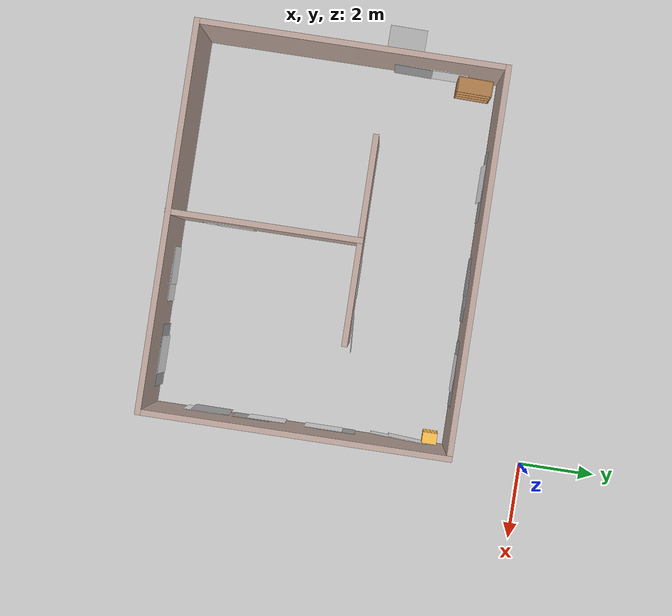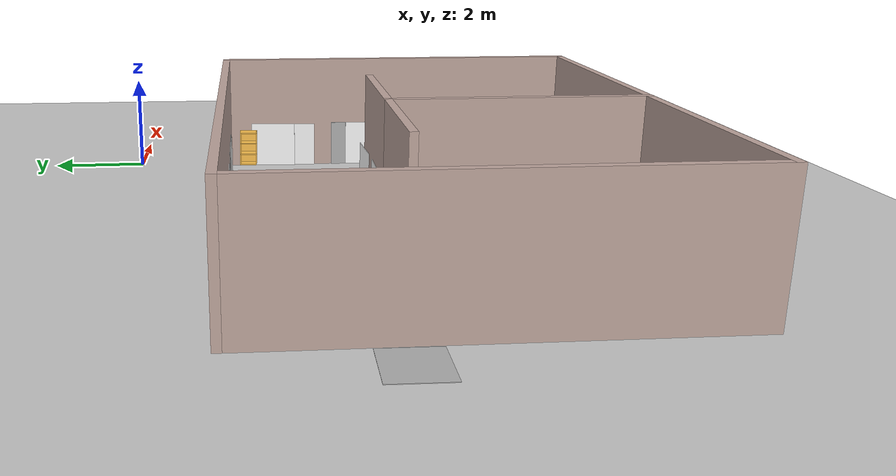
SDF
<sdf version="1.6">
 <world name="default">
  <light name="sun" type="directional">
   <pose>0 0 10 0 -0 0</pose>
   <diffuse>0.8 0.8 0.8 1</diffuse>
   <specular>0.1 0.1 0.1 1</specular>
   <attenuation>
    <range>1000</range>
    <constant>0.9</constant>
    <linear>0.01</linear>
    <quadratic>0.001</quadratic>
   </attenuation>
   <direction>-0.5 0.5 -1</direction>
  </light>
  <model name="ground_plane">
   <static>1</static>
   <link name="link">
    <collision name="collision">
     <geometry><plane><normal>0 0 1</normal><size>100 100</size></plane></geometry>
     <surface><friction><ode><mu>100</mu><mu2>50</mu2></ode></friction></surface>
    </collision>
    <visual name="visual">
     <cast_shadows>0</cast_shadows>
     <geometry><plane><normal>0 0 1</normal><size>100 100</size></plane></geometry>
     <material>
      <script><uri>file://media/materials/scripts/gazebo.material</uri><name>Gazebo/Grey</name></script>
     </material>
    </visual>
   </link>
  </model>
  <gravity>0 0 -9.8</gravity>
  <magnetic_field>6e-06 2.3e-05 -4.2e-05</magnetic_field>
  <atmosphere type="adiabatic"/>
  <physics name="default_physics" default="0" type="ode">
   <max_step_size>0.001</max_step_size>
   <real_time_factor>1</real_time_factor>
   <real_time_update_rate>1000</real_time_update_rate>
  </physics>
  <scene><ambient>0.4 0.4 0.4 1</ambient><background>0.7 0.7 0.7 1</background><shadows>1</shadows></scene>
  <spherical_coordinates>
   <surface_model>EARTH_WGS84</surface_model>
   <latitude_deg>0</latitude_deg>
   <longitude_deg>0</longitude_deg>
   <elevation>0</elevation>
   <heading_deg>0</heading_deg>
  </spherical_coordinates>
  <model name="empty_room_colored_walls">
   <pose>-5.06103 -5.97507 0 0 -0 0</pose>
   <link name="Wall_62">
    <collision name="Wall_62_Collision">
     <geometry><box><size>10 0.15 2.5</size></box></geometry>
     <pose>0 0 1.25 0 -0 0</pose>
    </collision>
    <visual name="Wall_62_Visual">
     <pose>0 0 1.25 0 -0 0</pose>
     <geometry><box><size>10 0.15 2.5</size></box></geometry>
     <material>
      <script><uri>file://media/materials/scripts/gazebo.material</uri><name>Gazebo/Grey</name></script>
      <ambient>0.760784 0.662745 0.627451 1</ambient>
     </material>
    </visual>
    <pose>0 -3.92179 0 0 -0 0</pose>
   </link>
   <link name="Wall_63">
    <collision name="Wall_63_Collision">
     <geometry><box><size>8 0.15 2.5</size></box></geometry>
     <pose>0 0 1.25 0 -0 0</pose>
    </collision>
    <visual name="Wall_63_Visual">
     <pose>0 0 1.25 0 -0 0</pose>
     <geometry><box><size>8 0.15 2.5</size></box></geometry>
     <material>
      <script><uri>file://media/materials/scripts/gazebo.material</uri><name>Gazebo/Grey</name></script>
      <ambient>0.760784 0.662745 0.627451 1</ambient>
     </material>
    </visual>
    <pose>4.925 0.003206 0 0 -0 1.5708</pose>
   </link>
   <link name="Wall_64">
    <collision name="Wall_64_Collision">
     <geometry><box><size>10 0.15 2.5</size></box></geometry>
     <pose>0 0 1.25 0 -0 0</pose>
    </collision>
    <visual name="Wall_64_Visual">
     <pose>0 0 1.25 0 -0 0</pose>
     <geometry><box><size>10 0.15 2.5</size></box></geometry>
     <material>
      <script><uri>file://media/materials/scripts/gazebo.material</uri><name>Gazebo/Grey</name></script>
      <ambient>0.760784 0.662745 0.627451 1</ambient>
     </material>
    </visual>
    <pose>0 3.92821 0 0 -0 3.14159</pose>
   </link>
   <link name="Wall_65">
    <collision name="Wall_65_Collision">
     <geometry><box><size>8 0.15 2.5</size></box></geometry>
     <pose>0 0 1.25 0 -0 0</pose>
    </collision>
    <visual name="Wall_65_Visual">
     <pose>0 0 1.25 0 -0 0</pose>
     <geometry><box><size>8 0.15 2.5</size></box></geometry>
     <material>
      <script><uri>file://media/materials/scripts/gazebo.material</uri><name>Gazebo/Grey</name></script>
      <ambient>0.760784 0.662745 0.627451 1</ambient>
     </material>
    </visual>
    <pose>-4.925 0.003206 0 0 0 -1.5708</pose>
   </link>
   <link name="Wall_70">
    <collision name="Wall_70_Collision">
     <geometry><box><size>5 0.15 2.5</size></box></geometry>
     <pose>0 0 1.25 0 -0 0</pose>
    </collision>
    <visual name="Wall_70_Visual">
     <pose>0 0 1.25 0 -0 0</pose>
     <geometry><box><size>5 0.15 2.5</size></box></geometry>
     <material>
      <script><uri>file://media/materials/scripts/gazebo.material</uri><name>Gazebo/Grey</name></script>
      <ambient>0.760784 0.662745 0.627451 1</ambient>
     </material>
    </visual>
    <pose>-0.121943 -1.50321 0 0 -0 1.5708</pose>
   </link>
   <link name="Wall_71">
    <collision name="Wall_71_Collision">
     <geometry><box><size>2.75 0.15 2.5</size></box></geometry>
     <pose>0 0 1.25 0 -0 0</pose>
    </collision>
    <visual name="Wall_71_Visual">
     <pose>0 0 1.25 0 -0 0</pose>
     <geometry><box><size>2.75 0.15 2.5</size></box></geometry>
     <material>
      <script><uri>file://media/materials/scripts/gazebo.material</uri><name>Gazebo/Grey</name></script>
      <ambient>0.760784 0.662745 0.627451 1</ambient>
     </material>
    </visual>
    <pose>1.17806 0.921794 0 0 -0 0</pose>
   </link>
   <link name="Wall_73">
    <collision name="Wall_73_Collision">
     <geometry><box><size>2.75 0.15 2.5</size></box></geometry>
     <pose>0 0 1.25 0 -0 0</pose>
    </collision>
    <visual name="Wall_73_Visual">
     <pose>0 0 1.25 0 -0 0</pose>
     <geometry><box><size>2.75 0.15 2.5</size></box></geometry>
     <material>
      <script><uri>file://media/materials/scripts/gazebo.material</uri><name>Gazebo/Grey</name></script>
      <ambient>0.760784 0.662745 0.627451 1</ambient>
     </material>
    </visual>
    <pose>-1.42194 0.921794 0 0 -0 3.14159</pose>
   </link>
   <static>1</static>
  </model>
  <model name="bookshelf">
   <static>1</static>
   <link name="link">
    <inertial><mass>1</mass></inertial>
    <collision name="back">
     <pose>0 0.005 0.6 0 -0 0</pose>
     <geometry><box><size>0.9 0.01 1.2</size></box></geometry>
    </collision>
    <visual name="visual1">
     <pose>0 0.005 0.6 0 -0 0</pose>
     <geometry><box><size>0.9 0.01 1.2</size></box></geometry>
     <material>
      <script><uri>file://media/materials/scripts/gazebo.material</uri><name>Gazebo/Wood</name></script>
     </material>
    </visual>
    <collision name="left_side">
     <pose>0.45 -0.195 0.6 0 -0 0</pose>
     <geometry><box><size>0.02 0.4 1.2</size></box></geometry>
    </collision>
    <visual name="visual2">
     <pose>0.45 -0.195 0.6 0 -0 0</pose>
     <geometry><box><size>0.02 0.4 1.2</size></box></geometry>
     <material>
      <script><uri>file://media/materials/scripts/gazebo.material</uri><name>Gazebo/Wood</name></script>
     </material>
    </visual>
    <collision name="right_side">
     <pose>-0.45 -0.195 0.6 0 -0 0</pose>
     <geometry><box><size>0.02 0.4 1.2</size></box></geometry>
    </collision>
    <visual name="visual3">
     <pose>-0.45 -0.195 0.6 0 -0 0</pose>
     <geometry><box><size>0.02 0.4 1.2</size></box></geometry>
     <material>
      <script><uri>file://media/materials/scripts/gazebo.material</uri><name>Gazebo/Wood</name></script>
     </material>
    </visual>
    <collision name="bottom">
     <pose>0 -0.195 0.03 0 -0 0</pose>
     <geometry><box><size>0.88 0.4 0.06</size></box></geometry>
    </collision>
    <visual name="visual4">
     <pose>0 -0.195 0.03 0 -0 0</pose>
     <geometry><box><size>0.88 0.4 0.06</size></box></geometry>
     <material>
      <script><uri>file://media/materials/scripts/gazebo.material</uri><name>Gazebo/Wood</name></script>
     </material>
    </visual>
    <collision name="top">
     <pose>0 -0.195 1.19 0 -0 0</pose>
     <geometry><box><size>0.88 0.4 0.02</size></box></geometry>
    </collision>
    <visual name="visual5">
     <pose>0 -0.195 1.19 0 -0 0</pose>
     <geometry><box><size>0.88 0.4 0.02</size></box></geometry>
     <material>
      <script><uri>file://media/materials/scripts/gazebo.material</uri><name>Gazebo/Wood</name></script>
     </material>
    </visual>
    <collision name="low_shelf">
     <pose>0 -0.195 0.43 0 -0 0</pose>
     <geometry><box><size>0.88 0.4 0.02</size></box></geometry>
    </collision>
    <visual name="visual6">
     <pose>0 -0.195 0.43 0 -0 0</pose>
     <geometry><box><size>0.88 0.4 0.02</size></box></geometry>
     <material>
      <script><uri>file://media/materials/scripts/gazebo.material</uri><name>Gazebo/Wood</name></script>
     </material>
    </visual>
    <collision name="high_shelf">
     <pose>0 -0.195 0.8 0 -0 0</pose>
     <geometry><box><size>0.88 0.4 0.02</size></box></geometry>
    </collision>
    <visual name="visual7">
     <pose>0 -0.195 0.8 0 -0 0</pose>
     <geometry><box><size>0.88 0.4 0.02</size></box></geometry>
     <material>
      <script><uri>file://media/materials/scripts/gazebo.material</uri><name>Gazebo/Wood</name></script>
     </material>
    </visual>
   </link>
   <pose>-9.80012 -2.72902 0 0 -0 1.5503</pose>
  </model>
  <model name="Gas_2">
   <link name="link_0">
    <pose>4e-06 0 0 0 -0 0</pose>
    <inertial>
     <mass>1</mass>
     <inertia>
      <ixx>0.166667</ixx>
      <ixy>0</ixy>
      <ixz>0</ixz>
      <iyy>0.166667</iyy>
      <iyz>0</iyz>
      <izz>0.166667</izz>
     </inertia>
    </inertial>
    <visual name="visual">
     <geometry><box><size>0.01 1 1</size></box></geometry>
     <material>
      <lighting>1</lighting>
      <script>
       <uri>model://gas_2_N/materials/scripts</uri>
       <uri>model://gas_2_N/materials/textures</uri>
       <name>Gas/Gas2N</name>
      </script>
      <ambient>1 1 1 1</ambient>
      <diffuse>1 1 1 1</diffuse>
      <specular>0.01 0.01 0.01 1</specular>
      <emissive>1 1 1 1</emissive>
     </material>
     <cast_shadows>0</cast_shadows>
    </visual>
    <collision name="collision">
     <geometry><box><size>0.01 1 1</size></box></geometry>
     <surface>
      <friction>
       <ode><mu>1</mu><mu2>1</mu2><fdir1>0 0 0</fdir1><slip1>0</slip1><slip2>0</slip2></ode>
       <torsional>
        <coefficient>1</coefficient>
        <patch_radius>0</patch_radius>
        <surface_radius>0</surface_radius>
        <use_patch_radius>1</use_patch_radius>
        <ode><slip>0</slip></ode>
       </torsional>
      </friction>
      <bounce><restitution_coefficient>0</restitution_coefficient><threshold>1e+06</threshold></bounce>
      <contact>
       <collide_without_contact>0</collide_without_contact>
       <collide_without_contact_bitmask>1</collide_without_contact_bitmask>
       <collide_bitmask>1</collide_bitmask>
       <ode>
        <soft_cfm>0</soft_cfm>
        <soft_erp>0.2</soft_erp>
        <kp>1e+13</kp>
        <kd>1</kd>
        <max_vel>0.01</max_vel>
        <min_depth>0</min_depth>
       </ode>
       <bullet>
        <split_impulse>1</split_impulse>
        <split_impulse_penetration_threshold>-0.01</split_impulse_penetration_threshold>
        <soft_cfm>0</soft_cfm>
        <soft_erp>0.2</soft_erp>
        <kp>1e+13</kp>
        <kd>1</kd>
       </bullet>
      </contact>
     </surface>
    </collision>
   </link>
   <static>0</static>
   <pose>-0.222112 -8.4847 0.499972 -6e-06 0.007088 -0.005093</pose>
  </model>
  <model name="Gas_3">
   <link name="link_0">
    <pose>4e-06 0 0 0 -0 0</pose>
    <inertial>
     <mass>1</mass>
     <inertia>
      <ixx>0.166667</ixx>
      <ixy>0</ixy>
      <ixz>0</ixz>
      <iyy>0.166667</iyy>
      <iyz>0</iyz>
      <izz>0.166667</izz>
     </inertia>
    </inertial>
    <visual name="visual">
     <geometry><box><size>0.01 1 1</size></box></geometry>
     <material>
      <lighting>1</lighting>
      <script>
       <uri>model://gas_3_N/materials/scripts</uri>
       <uri>model://gas_3_N/materials/textures</uri>
       <name>Gas/Gas3N</name>
      </script>
      <ambient>1 1 1 1</ambient>
      <diffuse>1 1 1 1</diffuse>
      <specular>0.01 0.01 0.01 1</specular>
      <emissive>1 1 1 1</emissive>
     </material>
     <cast_shadows>0</cast_shadows>
    </visual>
    <collision name="collision">
     <geometry><box><size>0.01 1 1</size></box></geometry>
     <surface>
      <friction>
       <ode><mu>1</mu><mu2>1</mu2><fdir1>0 0 0</fdir1><slip1>0</slip1><slip2>0</slip2></ode>
       <torsional>
        <coefficient>1</coefficient>
        <patch_radius>0</patch_radius>
        <surface_radius>0</surface_radius>
        <use_patch_radius>1</use_patch_radius>
        <ode><slip>0</slip></ode>
       </torsional>
      </friction>
      <bounce><restitution_coefficient>0</restitution_coefficient><threshold>1e+06</threshold></bounce>
      <contact>
       <collide_without_contact>0</collide_without_contact>
       <collide_without_contact_bitmask>1</collide_without_contact_bitmask>
       <collide_bitmask>1</collide_bitmask>
       <ode>
        <soft_cfm>0</soft_cfm>
        <soft_erp>0.2</soft_erp>
        <kp>1e+13</kp>
        <kd>1</kd>
        <max_vel>0.01</max_vel>
        <min_depth>0</min_depth>
       </ode>
       <bullet>
        <split_impulse>1</split_impulse>
        <split_impulse_penetration_threshold>-0.01</split_impulse_penetration_threshold>
        <soft_cfm>0</soft_cfm>
        <soft_erp>0.2</soft_erp>
        <kp>1e+13</kp>
        <kd>1</kd>
       </bullet>
      </contact>
     </surface>
    </collision>
   </link>
   <static>0</static>
   <pose>-3.42391 -9.81438 0.5 0 2e-06 -1.56585</pose>
  </model>
  <model name="Gas_4_1">
   <link name="link_0">
    <pose>4e-06 0 0 0 -0 0</pose>
    <inertial>
     <mass>1</mass>
     <inertia>
      <ixx>0.166667</ixx>
      <ixy>0</ixy>
      <ixz>0</ixz>
      <iyy>0.166667</iyy>
      <iyz>0</iyz>
      <izz>0.166667</izz>
     </inertia>
    </inertial>
    <visual name="visual">
     <geometry><box><size>0.01 1 1</size></box></geometry>
     <material>
      <lighting>1</lighting>
      <script>
       <uri>model://gas_4_N/materials/scripts</uri>
       <uri>model://gas_4_N/materials/textures</uri>
       <name>Gas/Gas4N</name>
      </script>
      <ambient>1 1 1 1</ambient>
      <diffuse>1 1 1 1</diffuse>
      <specular>0.01 0.01 0.01 1</specular>
      <emissive>1 1 1 1</emissive>
     </material>
     <cast_shadows>0</cast_shadows>
    </visual>
    <collision name="collision">
     <geometry><box><size>0.01 1 1</size></box></geometry>
     <surface>
      <friction>
       <ode><mu>1</mu><mu2>1</mu2><fdir1>0 0 0</fdir1><slip1>0</slip1><slip2>0</slip2></ode>
       <torsional>
        <coefficient>1</coefficient>
        <patch_radius>0</patch_radius>
        <surface_radius>0</surface_radius>
        <use_patch_radius>1</use_patch_radius>
        <ode><slip>0</slip></ode>
       </torsional>
      </friction>
      <bounce><restitution_coefficient>0</restitution_coefficient><threshold>1e+06</threshold></bounce>
      <contact>
       <collide_without_contact>0</collide_without_contact>
       <collide_without_contact_bitmask>1</collide_without_contact_bitmask>
       <collide_bitmask>1</collide_bitmask>
       <ode>
        <soft_cfm>0</soft_cfm>
        <soft_erp>0.2</soft_erp>
        <kp>1e+13</kp>
        <kd>1</kd>
        <max_vel>0.01</max_vel>
        <min_depth>0</min_depth>
       </ode>
       <bullet>
        <split_impulse>1</split_impulse>
        <split_impulse_penetration_threshold>-0.01</split_impulse_penetration_threshold>
        <soft_cfm>0</soft_cfm>
        <soft_erp>0.2</soft_erp>
        <kp>1e+13</kp>
        <kd>1</kd>
       </bullet>
      </contact>
     </surface>
    </collision>
   </link>
   <static>0</static>
   <pose>-1.50529 -9.77758 0.499816 -0 -0.038214 1.57007</pose>
  </model>
  <model name="Gas_1_0">
   <link name="link_0">
    <pose>4e-06 0 0 0 -0 0</pose>
    <inertial>
     <mass>1</mass>
     <inertia>
      <ixx>0.166667</ixx>
      <ixy>0</ixy>
      <ixz>0</ixz>
      <iyy>0.166667</iyy>
      <iyz>0</iyz>
      <izz>0.166667</izz>
     </inertia>
    </inertial>
    <visual name="visual">
     <geometry><box><size>0.01 1 1</size></box></geometry>
     <material>
      <lighting>1</lighting>
      <script>
       <uri>model://gas_1_N/materials/scripts</uri>
       <uri>model://gas_1_N/materials/textures</uri>
       <name>Gas/Gas1N</name>
      </script>
      <ambient>1 1 1 1</ambient>
      <diffuse>1 1 1 1</diffuse>
      <specular>0.01 0.01 0.01 1</specular>
      <emissive>1 1 1 1</emissive>
     </material>
     <cast_shadows>0</cast_shadows>
    </visual>
    <collision name="collision">
     <geometry><box><size>0.01 1 1</size></box></geometry>
     <surface>
      <friction>
       <ode><mu>1</mu><mu2>1</mu2><fdir1>0 0 0</fdir1><slip1>0</slip1><slip2>0</slip2></ode>
       <torsional>
        <coefficient>1</coefficient>
        <patch_radius>0</patch_radius>
        <surface_radius>0</surface_radius>
        <use_patch_radius>1</use_patch_radius>
        <ode><slip>0</slip></ode>
       </torsional>
      </friction>
      <bounce><restitution_coefficient>0</restitution_coefficient><threshold>1e+06</threshold></bounce>
      <contact>
       <collide_without_contact>0</collide_without_contact>
       <collide_without_contact_bitmask>1</collide_without_contact_bitmask>
       <collide_bitmask>1</collide_bitmask>
       <ode>
        <soft_cfm>0</soft_cfm>
        <soft_erp>0.2</soft_erp>
        <kp>1e+13</kp>
        <kd>1</kd>
        <max_vel>0.01</max_vel>
        <min_depth>0</min_depth>
       </ode>
       <bullet>
        <split_impulse>1</split_impulse>
        <split_impulse_penetration_threshold>-0.01</split_impulse_penetration_threshold>
        <soft_cfm>0</soft_cfm>
        <soft_erp>0.2</soft_erp>
        <kp>1e+13</kp>
        <kd>1</kd>
       </bullet>
      </contact>
     </surface>
    </collision>
   </link>
   <static>0</static>
   <pose>-0.236814 -6.81898 0.5 0 -2e-06 0.002062</pose>
  </model>
  <model name="Gas_4_0">
   <link name="link_0">
    <pose>4e-06 0 0 0 -0 0</pose>
    <inertial>
     <mass>1</mass>
     <inertia>
      <ixx>0.166667</ixx>
      <ixy>0</ixy>
      <ixz>0</ixz>
      <iyy>0.166667</iyy>
      <iyz>0</iyz>
      <izz>0.166667</izz>
     </inertia>
    </inertial>
    <visual name="visual">
     <geometry><box><size>0.01 1 1</size></box></geometry>
     <material>
      <lighting>1</lighting>
      <script>
       <uri>model://gas_4_N/materials/scripts</uri>
       <uri>model://gas_4_N/materials/textures</uri>
       <name>Gas/Gas4N</name>
      </script>
      <ambient>1 1 1 1</ambient>
      <diffuse>1 1 1 1</diffuse>
      <specular>0.01 0.01 0.01 1</specular>
      <emissive>1 1 1 1</emissive>
     </material>
     <cast_shadows>0</cast_shadows>
    </visual>
    <collision name="collision">
     <geometry><box><size>0.01 1 1</size></box></geometry>
     <surface>
      <friction>
       <ode><mu>1</mu><mu2>1</mu2><fdir1>0 0 0</fdir1><slip1>0</slip1><slip2>0</slip2></ode>
       <torsional>
        <coefficient>1</coefficient>
        <patch_radius>0</patch_radius>
        <surface_radius>0</surface_radius>
        <use_patch_radius>1</use_patch_radius>
        <ode><slip>0</slip></ode>
       </torsional>
      </friction>
      <bounce><restitution_coefficient>0</restitution_coefficient><threshold>1e+06</threshold></bounce>
      <contact>
       <collide_without_contact>0</collide_without_contact>
       <collide_without_contact_bitmask>1</collide_without_contact_bitmask>
       <collide_bitmask>1</collide_bitmask>
       <ode>
        <soft_cfm>0</soft_cfm>
        <soft_erp>0.2</soft_erp>
        <kp>1e+13</kp>
        <kd>1</kd>
        <max_vel>0.01</max_vel>
        <min_depth>0</min_depth>
       </ode>
       <bullet>
        <split_impulse>1</split_impulse>
        <split_impulse_penetration_threshold>-0.01</split_impulse_penetration_threshold>
        <soft_cfm>0</soft_cfm>
        <soft_erp>0.2</soft_erp>
        <kp>1e+13</kp>
        <kd>1</kd>
       </bullet>
      </contact>
     </surface>
    </collision>
   </link>
   <static>0</static>
   <pose>-0.234542 -5.30976 0.5 0 -1e-06 -0.000196</pose>
  </model>
  <model name="Gas_3_1">
   <link name="link_0">
    <pose>4e-06 0 0 0 -0 0</pose>
    <inertial>
     <mass>1</mass>
     <inertia>
      <ixx>0.166667</ixx>
      <ixy>0</ixy>
      <ixz>0</ixz>
      <iyy>0.166667</iyy>
      <iyz>0</iyz>
      <izz>0.166667</izz>
     </inertia>
    </inertial>
    <visual name="visual">
     <geometry><box><size>0.01 1 1</size></box></geometry>
     <material>
      <lighting>1</lighting>
      <script>
       <uri>model://gas_3_N/materials/scripts</uri>
       <uri>model://gas_3_N/materials/textures</uri>
       <name>Gas/Gas3N</name>
      </script>
      <ambient>1 1 1 1</ambient>
      <diffuse>1 1 1 1</diffuse>
      <specular>0.01 0.01 0.01 1</specular>
      <emissive>1 1 1 1</emissive>
     </material>
     <cast_shadows>0</cast_shadows>
    </visual>
    <collision name="collision">
     <geometry><box><size>0.01 1 1</size></box></geometry>
     <surface>
      <friction>
       <ode><mu>1</mu><mu2>1</mu2><fdir1>0 0 0</fdir1><slip1>0</slip1><slip2>0</slip2></ode>
       <torsional>
        <coefficient>1</coefficient>
        <patch_radius>0</patch_radius>
        <surface_radius>0</surface_radius>
        <use_patch_radius>1</use_patch_radius>
        <ode><slip>0</slip></ode>
       </torsional>
      </friction>
      <bounce><restitution_coefficient>0</restitution_coefficient><threshold>1e+06</threshold></bounce>
      <contact>
       <collide_without_contact>0</collide_without_contact>
       <collide_without_contact_bitmask>1</collide_without_contact_bitmask>
       <collide_bitmask>1</collide_bitmask>
       <ode>
        <soft_cfm>0</soft_cfm>
        <soft_erp>0.2</soft_erp>
        <kp>1e+13</kp>
        <kd>1</kd>
        <max_vel>0.01</max_vel>
        <min_depth>0</min_depth>
       </ode>
       <bullet>
        <split_impulse>1</split_impulse>
        <split_impulse_penetration_threshold>-0.01</split_impulse_penetration_threshold>
        <soft_cfm>0</soft_cfm>
        <soft_erp>0.2</soft_erp>
        <kp>1e+13</kp>
        <kd>1</kd>
       </bullet>
      </contact>
     </surface>
    </collision>
   </link>
   <static>0</static>
   <pose>-0.266643 -3.56804 0.499694 0 -0.046381 -0.054955</pose>
  </model>
  <model name="Gas_1_2">
   <link name="link_0">
    <pose>4e-06 0 0 0 -0 0</pose>
    <inertial>
     <mass>1</mass>
     <inertia>
      <ixx>0.166667</ixx>
      <ixy>0</ixy>
      <ixz>0</ixz>
      <iyy>0.166667</iyy>
      <iyz>0</iyz>
      <izz>0.166667</izz>
     </inertia>
    </inertial>
    <visual name="visual">
     <geometry><box><size>0.01 1 1</size></box></geometry>
     <material>
      <lighting>1</lighting>
      <script>
       <uri>model://gas_1_N/materials/scripts</uri>
       <uri>model://gas_1_N/materials/textures</uri>
       <name>Gas/Gas1N</name>
      </script>
      <ambient>1 1 1 1</ambient>
      <diffuse>1 1 1 1</diffuse>
      <specular>0.01 0.01 0.01 1</specular>
      <emissive>1 1 1 1</emissive>
     </material>
     <cast_shadows>0</cast_shadows>
    </visual>
    <collision name="collision">
     <geometry><box><size>0.01 1 1</size></box></geometry>
     <surface>
      <friction>
       <ode><mu>1</mu><mu2>1</mu2><fdir1>0 0 0</fdir1><slip1>0</slip1><slip2>0</slip2></ode>
       <torsional>
        <coefficient>1</coefficient>
        <patch_radius>0</patch_radius>
        <surface_radius>0</surface_radius>
        <use_patch_radius>1</use_patch_radius>
        <ode><slip>0</slip></ode>
       </torsional>
      </friction>
      <bounce><restitution_coefficient>0</restitution_coefficient><threshold>1e+06</threshold></bounce>
      <contact>
       <collide_without_contact>0</collide_without_contact>
       <collide_without_contact_bitmask>1</collide_without_contact_bitmask>
       <collide_bitmask>1</collide_bitmask>
       <ode>
        <soft_cfm>0</soft_cfm>
        <soft_erp>0.2</soft_erp>
        <kp>1e+13</kp>
        <kd>1</kd>
        <max_vel>0.01</max_vel>
        <min_depth>0</min_depth>
       </ode>
       <bullet>
        <split_impulse>1</split_impulse>
        <split_impulse_penetration_threshold>-0.01</split_impulse_penetration_threshold>
        <soft_cfm>0</soft_cfm>
        <soft_erp>0.2</soft_erp>
        <kp>1e+13</kp>
        <kd>1</kd>
       </bullet>
      </contact>
     </surface>
    </collision>
   </link>
   <static>0</static>
   <pose>-2.16004 -2.14796 0.5 -0 -2e-06 1.56216</pose>
  </model>
  <model name="Gas_2_0">
   <link name="link_0">
    <pose>4e-06 0 0 0 -0 0</pose>
    <inertial>
     <mass>1</mass>
     <inertia>
      <ixx>0.166667</ixx>
      <ixy>0</ixy>
      <ixz>0</ixz>
      <iyy>0.166667</iyy>
      <iyz>0</iyz>
      <izz>0.166667</izz>
     </inertia>
    </inertial>
    <visual name="visual">
     <geometry><box><size>0.01 1 1</size></box></geometry>
     <material>
      <lighting>1</lighting>
      <script>
       <uri>model://gas_2_N/materials/scripts</uri>
       <uri>model://gas_2_N/materials/textures</uri>
       <name>Gas/Gas2N</name>
      </script>
      <ambient>1 1 1 1</ambient>
      <diffuse>1 1 1 1</diffuse>
      <specular>0.01 0.01 0.01 1</specular>
      <emissive>1 1 1 1</emissive>
     </material>
     <cast_shadows>0</cast_shadows>
    </visual>
    <collision name="collision">
     <geometry><box><size>0.01 1 1</size></box></geometry>
     <surface>
      <friction>
       <ode><mu>1</mu><mu2>1</mu2><fdir1>0 0 0</fdir1><slip1>0</slip1><slip2>0</slip2></ode>
       <torsional>
        <coefficient>1</coefficient>
        <patch_radius>0</patch_radius>
        <surface_radius>0</surface_radius>
        <use_patch_radius>1</use_patch_radius>
        <ode><slip>0</slip></ode>
       </torsional>
      </friction>
      <bounce><restitution_coefficient>0</restitution_coefficient><threshold>1e+06</threshold></bounce>
      <contact>
       <collide_without_contact>0</collide_without_contact>
       <collide_without_contact_bitmask>1</collide_without_contact_bitmask>
       <collide_bitmask>1</collide_bitmask>
       <ode>
        <soft_cfm>0</soft_cfm>
        <soft_erp>0.2</soft_erp>
        <kp>1e+13</kp>
        <kd>1</kd>
        <max_vel>0.01</max_vel>
        <min_depth>0</min_depth>
       </ode>
       <bullet>
        <split_impulse>1</split_impulse>
        <split_impulse_penetration_threshold>-0.01</split_impulse_penetration_threshold>
        <soft_cfm>0</soft_cfm>
        <soft_erp>0.2</soft_erp>
        <kp>1e+13</kp>
        <kd>1</kd>
       </bullet>
      </contact>
     </surface>
    </collision>
   </link>
   <static>0</static>
   <pose>-4.38307 -2.13439 0.5 0 -2e-06 1.56691</pose>
  </model>
  <model name="Gas_3_2">
   <link name="link_0">
    <pose>4e-06 0 0 0 -0 0</pose>
    <inertial>
     <mass>1</mass>
     <inertia>
      <ixx>0.166667</ixx>
      <ixy>0</ixy>
      <ixz>0</ixz>
      <iyy>0.166667</iyy>
      <iyz>0</iyz>
      <izz>0.166667</izz>
     </inertia>
    </inertial>
    <visual name="visual">
     <geometry><box><size>0.01 1 1</size></box></geometry>
     <material>
      <lighting>1</lighting>
      <script>
       <uri>model://gas_3_N/materials/scripts</uri>
       <uri>model://gas_3_N/materials/textures</uri>
       <name>Gas/Gas3N</name>
      </script>
      <ambient>1 1 1 1</ambient>
      <diffuse>1 1 1 1</diffuse>
      <specular>0.01 0.01 0.01 1</specular>
      <emissive>1 1 1 1</emissive>
     </material>
     <cast_shadows>0</cast_shadows>
    </visual>
    <collision name="collision">
     <geometry><box><size>0.01 1 1</size></box></geometry>
     <surface>
      <friction>
       <ode><mu>1</mu><mu2>1</mu2><fdir1>0 0 0</fdir1><slip1>0</slip1><slip2>0</slip2></ode>
       <torsional>
        <coefficient>1</coefficient>
        <patch_radius>0</patch_radius>
        <surface_radius>0</surface_radius>
        <use_patch_radius>1</use_patch_radius>
        <ode><slip>0</slip></ode>
       </torsional>
      </friction>
      <bounce><restitution_coefficient>0</restitution_coefficient><threshold>1e+06</threshold></bounce>
      <contact>
       <collide_without_contact>0</collide_without_contact>
       <collide_without_contact_bitmask>1</collide_without_contact_bitmask>
       <collide_bitmask>1</collide_bitmask>
       <ode>
        <soft_cfm>0</soft_cfm>
        <soft_erp>0.2</soft_erp>
        <kp>1e+13</kp>
        <kd>1</kd>
        <max_vel>0.01</max_vel>
        <min_depth>0</min_depth>
       </ode>
       <bullet>
        <split_impulse>1</split_impulse>
        <split_impulse_penetration_threshold>-0.01</split_impulse_penetration_threshold>
        <soft_cfm>0</soft_cfm>
        <soft_erp>0.2</soft_erp>
        <kp>1e+13</kp>
        <kd>1</kd>
       </bullet>
      </contact>
     </surface>
    </collision>
   </link>
   <static>0</static>
   <pose>-4.23381 -4.97328 0.5 0 1e-06 1.5708</pose>
  </model>
  <model name="Gas_1_3">
   <link name="link_0">
    <pose>4e-06 0 0 0 -0 0</pose>
    <inertial>
     <mass>1</mass>
     <inertia>
      <ixx>0.166667</ixx>
      <ixy>0</ixy>
      <ixz>0</ixz>
      <iyy>0.166667</iyy>
      <iyz>0</iyz>
      <izz>0.166667</izz>
     </inertia>
    </inertial>
    <visual name="visual">
     <geometry><box><size>0.01 1 1</size></box></geometry>
     <material>
      <lighting>1</lighting>
      <script>
       <uri>model://gas_1_N/materials/scripts</uri>
       <uri>model://gas_1_N/materials/textures</uri>
       <name>Gas/Gas1N</name>
      </script>
      <ambient>1 1 1 1</ambient>
      <diffuse>1 1 1 1</diffuse>
      <specular>0.01 0.01 0.01 1</specular>
      <emissive>1 1 1 1</emissive>
     </material>
     <cast_shadows>0</cast_shadows>
    </visual>
    <collision name="collision">
     <geometry><box><size>0.01 1 1</size></box></geometry>
     <surface>
      <friction>
       <ode><mu>1</mu><mu2>1</mu2><fdir1>0 0 0</fdir1><slip1>0</slip1><slip2>0</slip2></ode>
       <torsional>
        <coefficient>1</coefficient>
        <patch_radius>0</patch_radius>
        <surface_radius>0</surface_radius>
        <use_patch_radius>1</use_patch_radius>
        <ode><slip>0</slip></ode>
       </torsional>
      </friction>
      <bounce><restitution_coefficient>0</restitution_coefficient><threshold>1e+06</threshold></bounce>
      <contact>
       <collide_without_contact>0</collide_without_contact>
       <collide_without_contact_bitmask>1</collide_without_contact_bitmask>
       <collide_bitmask>1</collide_bitmask>
       <ode>
        <soft_cfm>0</soft_cfm>
        <soft_erp>0.2</soft_erp>
        <kp>1e+13</kp>
        <kd>1</kd>
        <max_vel>0.01</max_vel>
        <min_depth>0</min_depth>
       </ode>
       <bullet>
        <split_impulse>1</split_impulse>
        <split_impulse_penetration_threshold>-0.01</split_impulse_penetration_threshold>
        <soft_cfm>0</soft_cfm>
        <soft_erp>0.2</soft_erp>
        <kp>1e+13</kp>
        <kd>1</kd>
       </bullet>
      </contact>
     </surface>
    </collision>
   </link>
   <static>0</static>
   <pose>-2.79683 -4.93888 0.5 0 -2e-06 1.63067</pose>
  </model>
  <model name="Gas_2_1">
   <link name="link_0">
    <pose>4e-06 0 0 0 -0 0</pose>
    <inertial>
     <mass>1</mass>
     <inertia>
      <ixx>0.166667</ixx>
      <ixy>0</ixy>
      <ixz>0</ixz>
      <iyy>0.166667</iyy>
      <iyz>0</iyz>
      <izz>0.166667</izz>
     </inertia>
    </inertial>
    <visual name="visual">
     <geometry><box><size>0.01 1 1</size></box></geometry>
     <material>
      <lighting>1</lighting>
      <script>
       <uri>model://gas_2_N/materials/scripts</uri>
       <uri>model://gas_2_N/materials/textures</uri>
       <name>Gas/Gas2N</name>
      </script>
      <ambient>1 1 1 1</ambient>
      <diffuse>1 1 1 1</diffuse>
      <specular>0.01 0.01 0.01 1</specular>
      <emissive>1 1 1 1</emissive>
     </material>
     <cast_shadows>0</cast_shadows>
    </visual>
    <collision name="collision">
     <geometry><box><size>0.01 1 1</size></box></geometry>
     <surface>
      <friction>
       <ode><mu>1</mu><mu2>1</mu2><fdir1>0 0 0</fdir1><slip1>0</slip1><slip2>0</slip2></ode>
       <torsional>
        <coefficient>1</coefficient>
        <patch_radius>0</patch_radius>
        <surface_radius>0</surface_radius>
        <use_patch_radius>1</use_patch_radius>
        <ode><slip>0</slip></ode>
       </torsional>
      </friction>
      <bounce><restitution_coefficient>0</restitution_coefficient><threshold>1e+06</threshold></bounce>
      <contact>
       <collide_without_contact>0</collide_without_contact>
       <collide_without_contact_bitmask>1</collide_without_contact_bitmask>
       <collide_bitmask>1</collide_bitmask>
       <ode>
        <soft_cfm>0</soft_cfm>
        <soft_erp>0.2</soft_erp>
        <kp>1e+13</kp>
        <kd>1</kd>
        <max_vel>0.01</max_vel>
        <min_depth>0</min_depth>
       </ode>
       <bullet>
        <split_impulse>1</split_impulse>
        <split_impulse_penetration_threshold>-0.01</split_impulse_penetration_threshold>
        <soft_cfm>0</soft_cfm>
        <soft_erp>0.2</soft_erp>
        <kp>1e+13</kp>
        <kd>1</kd>
       </bullet>
      </contact>
     </surface>
    </collision>
   </link>
   <static>0</static>
   <pose>-9.8861 -3.92126 0.499779 9e-06 -0.03988 -4e-06</pose>
  </model>
  <model name="Gas_4_2">
   <link name="link_0">
    <pose>4e-06 0 0 0 -0 0</pose>
    <inertial>
     <mass>1</mass>
     <inertia>
      <ixx>0.166667</ixx>
      <ixy>0</ixy>
      <ixz>0</ixz>
      <iyy>0.166667</iyy>
      <iyz>0</iyz>
      <izz>0.166667</izz>
     </inertia>
    </inertial>
    <visual name="visual">
     <geometry><box><size>0.01 1 1</size></box></geometry>
     <material>
      <lighting>1</lighting>
      <script>
       <uri>model://gas_4_N/materials/scripts</uri>
       <uri>model://gas_4_N/materials/textures</uri>
       <name>Gas/Gas4N</name>
      </script>
      <ambient>1 1 1 1</ambient>
      <diffuse>1 1 1 1</diffuse>
      <specular>0.01 0.01 0.01 1</specular>
      <emissive>1 1 1 1</emissive>
     </material>
     <cast_shadows>0</cast_shadows>
    </visual>
    <collision name="collision">
     <geometry><box><size>0.01 1 1</size></box></geometry>
     <surface>
      <friction>
       <ode><mu>1</mu><mu2>1</mu2><fdir1>0 0 0</fdir1><slip1>0</slip1><slip2>0</slip2></ode>
       <torsional>
        <coefficient>1</coefficient>
        <patch_radius>0</patch_radius>
        <surface_radius>0</surface_radius>
        <use_patch_radius>1</use_patch_radius>
        <ode><slip>0</slip></ode>
       </torsional>
      </friction>
      <bounce><restitution_coefficient>0</restitution_coefficient><threshold>1e+06</threshold></bounce>
      <contact>
       <collide_without_contact>0</collide_without_contact>
       <collide_without_contact_bitmask>1</collide_without_contact_bitmask>
       <collide_bitmask>1</collide_bitmask>
       <ode>
        <soft_cfm>0</soft_cfm>
        <soft_erp>0.2</soft_erp>
        <kp>1e+13</kp>
        <kd>1</kd>
        <max_vel>0.01</max_vel>
        <min_depth>0</min_depth>
       </ode>
       <bullet>
        <split_impulse>1</split_impulse>
        <split_impulse_penetration_threshold>-0.01</split_impulse_penetration_threshold>
        <soft_cfm>0</soft_cfm>
        <soft_erp>0.2</soft_erp>
        <kp>1e+13</kp>
        <kd>1</kd>
       </bullet>
      </contact>
     </surface>
    </collision>
   </link>
   <static>0</static>
   <pose>-7.19141 -2.1716 0.499645 3e-06 -0.049053 -1.57904</pose>
  </model>
  <model name="Gas_1_1">
   <link name="link_0">
    <pose>4e-06 0 0 0 -0 0</pose>
    <inertial>
     <mass>1</mass>
     <inertia>
      <ixx>0.166667</ixx>
      <ixy>0</ixy>
      <ixz>0</ixz>
      <iyy>0.166667</iyy>
      <iyz>0</iyz>
      <izz>0.166667</izz>
     </inertia>
    </inertial>
    <visual name="visual">
     <geometry><box><size>0.01 1 1</size></box></geometry>
     <material>
      <lighting>1</lighting>
      <script>
       <uri>model://gas_1_N/materials/scripts</uri>
       <uri>model://gas_1_N/materials/textures</uri>
       <name>Gas/Gas1N</name>
      </script>
      <ambient>1 1 1 1</ambient>
      <diffuse>1 1 1 1</diffuse>
      <specular>0.01 0.01 0.01 1</specular>
      <emissive>1 1 1 1</emissive>
     </material>
     <cast_shadows>0</cast_shadows>
    </visual>
    <collision name="collision">
     <geometry><box><size>0.01 1 1</size></box></geometry>
     <surface>
      <friction>
       <ode><mu>1</mu><mu2>1</mu2><fdir1>0 0 0</fdir1><slip1>0</slip1><slip2>0</slip2></ode>
       <torsional>
        <coefficient>1</coefficient>
        <patch_radius>0</patch_radius>
        <surface_radius>0</surface_radius>
        <use_patch_radius>1</use_patch_radius>
        <ode><slip>0</slip></ode>
       </torsional>
      </friction>
      <bounce><restitution_coefficient>0</restitution_coefficient><threshold>1e+06</threshold></bounce>
      <contact>
       <collide_without_contact>0</collide_without_contact>
       <collide_without_contact_bitmask>1</collide_without_contact_bitmask>
       <collide_bitmask>1</collide_bitmask>
       <ode>
        <soft_cfm>0</soft_cfm>
        <soft_erp>0.2</soft_erp>
        <kp>1e+13</kp>
        <kd>1</kd>
        <max_vel>0.01</max_vel>
        <min_depth>0</min_depth>
       </ode>
       <bullet>
        <split_impulse>1</split_impulse>
        <split_impulse_penetration_threshold>-0.01</split_impulse_penetration_threshold>
        <soft_cfm>0</soft_cfm>
        <soft_erp>0.2</soft_erp>
        <kp>1e+13</kp>
        <kd>1</kd>
       </bullet>
      </contact>
     </surface>
    </collision>
   </link>
   <static>0</static>
   <pose>-5.09178 -8.35994 0.5 0 2e-06 0.002339</pose>
  </model>
  <model name="Fire_1">
   <link name="link_0">
    <pose>4e-06 0 0 0 -0 0</pose>
    <inertial>
     <mass>1</mass>
     <inertia>
      <ixx>0.166667</ixx>
      <ixy>0</ixy>
      <ixz>0</ixz>
      <iyy>0.166667</iyy>
      <iyz>0</iyz>
      <izz>0.166667</izz>
     </inertia>
    </inertial>
    <visual name="visual">
     <geometry><box><size>0.01 1 1</size></box></geometry>
     <material>
      <lighting>1</lighting>
      <script>
       <uri>model://fire_1/materials/scripts</uri>
       <uri>model://fire_1/materials/textures</uri>
       <name>Fire/Fire1</name>
      </script>
      <ambient>1 1 1 1</ambient>
      <diffuse>1 1 1 1</diffuse>
      <specular>0.01 0.01 0.01 1</specular>
      <emissive>1 1 1 1</emissive>
     </material>
     <cast_shadows>0</cast_shadows>
    </visual>
    <collision name="collision">
     <geometry><box><size>0.01 1 1</size></box></geometry>
     <surface>
      <friction>
       <ode><mu>1</mu><mu2>1</mu2><fdir1>0 0 0</fdir1><slip1>0</slip1><slip2>0</slip2></ode>
       <torsional>
        <coefficient>1</coefficient>
        <patch_radius>0</patch_radius>
        <surface_radius>0</surface_radius>
        <use_patch_radius>1</use_patch_radius>
        <ode><slip>0</slip></ode>
       </torsional>
      </friction>
      <bounce><restitution_coefficient>0</restitution_coefficient><threshold>1e+06</threshold></bounce>
      <contact>
       <collide_without_contact>0</collide_without_contact>
       <collide_without_contact_bitmask>1</collide_without_contact_bitmask>
       <collide_bitmask>1</collide_bitmask>
       <ode>
        <soft_cfm>0</soft_cfm>
        <soft_erp>0.2</soft_erp>
        <kp>1e+13</kp>
        <kd>1</kd>
        <max_vel>0.01</max_vel>
        <min_depth>0</min_depth>
       </ode>
       <bullet>
        <split_impulse>1</split_impulse>
        <split_impulse_penetration_threshold>-0.01</split_impulse_penetration_threshold>
        <soft_cfm>0</soft_cfm>
        <soft_erp>0.2</soft_erp>
        <kp>1e+13</kp>
        <kd>1</kd>
       </bullet>
      </contact>
     </surface>
    </collision>
   </link>
   <static>0</static>
   <pose>-5.10297 -8.71783 0.5 -0 2e-06 4e-06</pose>
  </model>
  <model name="Fire_1_0">
   <link name="link_0">
    <pose>4e-06 0 0 0 -0 0</pose>
    <inertial>
     <mass>1</mass>
     <inertia>
      <ixx>0.166667</ixx>
      <ixy>0</ixy>
      <ixz>0</ixz>
      <iyy>0.166667</iyy>
      <iyz>0</iyz>
      <izz>0.166667</izz>
     </inertia>
    </inertial>
    <visual name="visual">
     <geometry><box><size>0.01 1 1</size></box></geometry>
     <material>
      <lighting>1</lighting>
      <script>
       <uri>model://fire_1/materials/scripts</uri>
       <uri>model://fire_1/materials/textures</uri>
       <name>Fire/Fire1</name>
      </script>
      <ambient>1 1 1 1</ambient>
      <diffuse>1 1 1 1</diffuse>
      <specular>0.01 0.01 0.01 1</specular>
      <emissive>1 1 1 1</emissive>
     </material>
     <cast_shadows>0</cast_shadows>
    </visual>
    <collision name="collision">
     <geometry><box><size>0.01 1 1</size></box></geometry>
     <surface>
      <friction>
       <ode><mu>1</mu><mu2>1</mu2><fdir1>0 0 0</fdir1><slip1>0</slip1><slip2>0</slip2></ode>
       <torsional>
        <coefficient>1</coefficient>
        <patch_radius>0</patch_radius>
        <surface_radius>0</surface_radius>
        <use_patch_radius>1</use_patch_radius>
        <ode><slip>0</slip></ode>
       </torsional>
      </friction>
      <bounce><restitution_coefficient>0</restitution_coefficient><threshold>1e+06</threshold></bounce>
      <contact>
       <collide_without_contact>0</collide_without_contact>
       <collide_without_contact_bitmask>1</collide_without_contact_bitmask>
       <collide_bitmask>1</collide_bitmask>
       <ode>
        <soft_cfm>0</soft_cfm>
        <soft_erp>0.2</soft_erp>
        <kp>1e+13</kp>
        <kd>1</kd>
        <max_vel>0.01</max_vel>
        <min_depth>0</min_depth>
       </ode>
       <bullet>
        <split_impulse>1</split_impulse>
        <split_impulse_penetration_threshold>-0.01</split_impulse_penetration_threshold>
        <soft_cfm>0</soft_cfm>
        <soft_erp>0.2</soft_erp>
        <kp>1e+13</kp>
        <kd>1</kd>
       </bullet>
      </contact>
     </surface>
    </collision>
   </link>
   <static>0</static>
   <pose>-3.86967 -9.80613 0.5 3.14159 6e-06 1.58398</pose>
  </model>
  <model name="Wall_Cabinet_15x30">
   <pose>-0.396854 -2.70414 0.461376 -1.54947 0 0</pose>
   <link name="Wall_0">
    <pose>0 0.374 0.192 0 -0 0</pose>
    <inertial>
     <mass>0.9882</mass>
     <inertia><ixx>0.0072</ixx><iyy>0.0194</iyy><izz>0.0122</izz><ixy>0</ixy><ixz>0</ixz><iyz>0</iyz></inertia>
    </inertial>
    <collision name="Wall_0_Collision"><geometry><box><size>0.296 0.02 0.384</size></box></geometry></collision>
    <visual name="Wall_0_Visual">
     <geometry><box><size>0.296 0.02 0.384</size></box></geometry>
     <material>
      <script><uri>file://media/materials/scripts/gazebo.material</uri><name>Gazebo/Grey</name></script>
      <ambient>1 0.764706 0.305882 1</ambient>
     </material>
    </visual>
   </link>
   <joint name="0_2" type="fixed">
    <pose>0 0 0.192 0 -0 0</pose>
    <parent>Wall_2</parent>
    <child>Wall_0</child>
    <axis>
     <xyz>0 0 1</xyz>
     <use_parent_model_frame>0</use_parent_model_frame>
     <limit><lower>-1e+16</lower><upper>1e+16</upper></limit>
    </axis>
   </joint>
   <joint name="0_4" type="fixed">
    <pose>0 0 -0.192 0 -0 0</pose>
    <parent>Wall_4</parent>
    <child>Wall_0</child>
    <axis>
     <xyz>0 0 1</xyz>
     <use_parent_model_frame>0</use_parent_model_frame>
     <limit><lower>-1e+16</lower><upper>1e+16</upper></limit>
    </axis>
   </joint>
   <joint name="0_15" type="fixed">
    <pose>0.148 0 0 0 -0 0</pose>
    <parent>Wall_15</parent>
    <child>Wall_0</child>
    <axis>
     <xyz>1 0 0</xyz>
     <use_parent_model_frame>0</use_parent_model_frame>
     <limit><lower>-1e+16</lower><upper>1e+16</upper></limit>
    </axis>
   </joint>
   <link name="Wall_11">
    <pose>0 -0.132768 0.192 0 -0 0</pose>
    <inertial>
     <mass>0.9882</mass>
     <inertia><ixx>0.0072</ixx><iyy>0.0194</iyy><izz>0.0122</izz><ixy>0</ixy><ixz>0</ixz><iyz>0</iyz></inertia>
    </inertial>
    <collision name="Wall_11_Collision"><geometry><box><size>0.296 0.02 0.384</size></box></geometry></collision>
    <visual name="Wall_11_Visual">
     <geometry><box><size>0.296 0.02 0.384</size></box></geometry>
     <material>
      <script><uri>file://media/materials/scripts/gazebo.material</uri><name>Gazebo/Grey</name></script>
      <ambient>1 0.764706 0.305882 1</ambient>
     </material>
    </visual>
   </link>
   <joint name="11_2" type="fixed">
    <pose>0 0 0.192 0 -0 0</pose>
    <parent>Wall_2</parent>
    <child>Wall_11</child>
    <axis>
     <xyz>0 0 1</xyz>
     <use_parent_model_frame>0</use_parent_model_frame>
     <limit><lower>-1e+16</lower><upper>1e+16</upper></limit>
    </axis>
   </joint>
   <joint name="11_4" type="fixed">
    <pose>0 0 -0.192 0 -0 0</pose>
    <parent>Wall_4</parent>
    <child>Wall_11</child>
    <axis>
     <xyz>0 0 1</xyz>
     <use_parent_model_frame>0</use_parent_model_frame>
     <limit><lower>-1e+16</lower><upper>1e+16</upper></limit>
    </axis>
   </joint>
   <joint name="11_15" type="fixed">
    <pose>0.148 0 0 0 -0 0</pose>
    <parent>Wall_15</parent>
    <child>Wall_11</child>
    <axis>
     <xyz>1 0 0</xyz>
     <use_parent_model_frame>0</use_parent_model_frame>
     <limit><lower>-1e+16</lower><upper>1e+16</upper></limit>
    </axis>
   </joint>
   <link name="Wall_15">
    <pose>0.138 0 0.19 0 -0 0</pose>
    <inertial>
     <mass>2.5241</mass>
     <inertia><ixx>0.0305</ixx><iyy>0.1229</iyy><izz>0.1532</izz><ixy>0</ixy><ixz>0</ixz><iyz>0</iyz></inertia>
    </inertial>
    <collision name="Wall_15_Collision"><geometry><box><size>0.02 0.764 0.38</size></box></geometry></collision>
    <visual name="Wall_15_Visual">
     <geometry><box><size>0.02 0.764 0.38</size></box></geometry>
     <material>
      <script><uri>file://media/materials/scripts/gazebo.material</uri><name>Gazebo/Grey</name></script>
      <ambient>1 0.764706 0.305882 1</ambient>
     </material>
    </visual>
   </link>
   <joint name="15_2" type="fixed">
    <pose>0 0 0.19 0 -0 0</pose>
    <parent>Wall_2</parent>
    <child>Wall_15</child>
    <axis>
     <xyz>0 0 1</xyz>
     <use_parent_model_frame>0</use_parent_model_frame>
     <limit><lower>-1e+16</lower><upper>1e+16</upper></limit>
    </axis>
   </joint>
   <joint name="15_4" type="fixed">
    <pose>0 0 -0.19 0 -0 0</pose>
    <parent>Wall_4</parent>
    <child>Wall_15</child>
    <axis>
     <xyz>0 0 1</xyz>
     <use_parent_model_frame>0</use_parent_model_frame>
     <limit><lower>-1e+16</lower><upper>1e+16</upper></limit>
    </axis>
   </joint>
   <link name="Wall_2">
    <pose>0 0 0.374 0 -0 0</pose>
    <inertial>
     <mass>1.9765</mass>
     <inertia><ixx>0.0145</ixx><iyy>0.1116</iyy><izz>0.0972</izz><ixy>0</ixy><ixz>0</ixz><iyz>0</iyz></inertia>
    </inertial>
    <collision name="Wall_2_Collision"><geometry><box><size>0.296 0.768 0.02</size></box></geometry></collision>
    <visual name="Wall_2_Visual">
     <geometry><box><size>0.296 0.768 0.02</size></box></geometry>
     <material>
      <script><uri>file://media/materials/scripts/gazebo.material</uri><name>Gazebo/Grey</name></script>
      <ambient>1 0.764706 0.305882 1</ambient>
     </material>
    </visual>
   </link>
   <link name="Wall_4">
    <pose>0 0 0.01 0 -0 0</pose>
    <inertial>
     <mass>1.9765</mass>
     <inertia><ixx>0.0145</ixx><iyy>0.1116</iyy><izz>0.0972</izz><ixy>0</ixy><ixz>0</ixz><iyz>0</iyz></inertia>
    </inertial>
    <collision name="Wall_4_Collision"><geometry><box><size>0.296 0.768 0.02</size></box></geometry></collision>
    <visual name="Wall_4_Visual">
     <geometry><box><size>0.296 0.768 0.02</size></box></geometry>
     <material>
      <script><uri>file://media/materials/scripts/gazebo.material</uri><name>Gazebo/Grey</name></script>
      <ambient>1 0.764706 0.305882 1</ambient>
     </material>
    </visual>
    <pose>-0.181124 0 0 0 0 -1.5708</pose>
   </link>
   <link name="Wall_6">
    <pose>0 -0.374 0.192 0 -0 0</pose>
    <inertial>
     <mass>0.9882</mass>
     <inertia><ixx>0.0072</ixx><iyy>0.0194</iyy><izz>0.0122</izz><ixy>0</ixy><ixz>0</ixz><iyz>0</iyz></inertia>
    </inertial>
    <collision name="Wall_6_Collision"><geometry><box><size>0.296 0.02 0.384</size></box></geometry></collision>
    <visual name="Wall_6_Visual">
     <geometry><box><size>0.296 0.02 0.384</size></box></geometry>
     <material>
      <script><uri>file://media/materials/scripts/gazebo.material</uri><name>Gazebo/Grey</name></script>
      <ambient>1 0.764706 0.305882 1</ambient>
     </material>
    </visual>
   </link>
   <joint name="6_2" type="fixed">
    <pose>0 0 0.192 0 -0 0</pose>
    <parent>Wall_2</parent>
    <child>Wall_6</child>
    <axis>
     <xyz>0 0 1</xyz>
     <use_parent_model_frame>0</use_parent_model_frame>
     <limit><lower>-1e+16</lower><upper>1e+16</upper></limit>
    </axis>
   </joint>
   <joint name="6_4" type="fixed">
    <pose>0 0 -0.192 0 -0 0</pose>
    <parent>Wall_4</parent>
    <child>Wall_6</child>
    <axis>
     <xyz>0 0 1</xyz>
     <use_parent_model_frame>0</use_parent_model_frame>
     <limit><lower>-1e+16</lower><upper>1e+16</upper></limit>
    </axis>
   </joint>
   <joint name="6_15" type="fixed">
    <pose>0.148 0 0 0 -0 0</pose>
    <parent>Wall_15</parent>
    <child>Wall_6</child>
    <axis>
     <xyz>1 0 0</xyz>
     <use_parent_model_frame>0</use_parent_model_frame>
     <limit><lower>-1e+16</lower><upper>1e+16</upper></limit>
    </axis>
   </joint>
   <link name="Wall_8">
    <pose>0 0.120833 0.192 0 -0 0</pose>
    <inertial>
     <mass>0.9882</mass>
     <inertia><ixx>0.0072</ixx><iyy>0.0194</iyy><izz>0.0122</izz><ixy>0</ixy><ixz>0</ixz><iyz>0</iyz></inertia>
    </inertial>
    <collision name="Wall_8_Collision"><geometry><box><size>0.296 0.02 0.384</size></box></geometry></collision>
    <visual name="Wall_8_Visual">
     <geometry><box><size>0.296 0.02 0.384</size></box></geometry>
     <material>
      <script><uri>file://media/materials/scripts/gazebo.material</uri><name>Gazebo/Grey</name></script>
      <ambient>1 0.764706 0.305882 1</ambient>
     </material>
    </visual>
   </link>
   <joint name="8_2" type="fixed">
    <pose>0 0 0.192 0 -0 0</pose>
    <parent>Wall_2</parent>
    <child>Wall_8</child>
    <axis>
     <xyz>0 0 1</xyz>
     <use_parent_model_frame>0</use_parent_model_frame>
     <limit><lower>-1e+16</lower><upper>1e+16</upper></limit>
    </axis>
   </joint>
   <joint name="8_4" type="fixed">
    <pose>0 0 -0.192 0 -0 0</pose>
    <parent>Wall_4</parent>
    <child>Wall_8</child>
    <axis>
     <xyz>0 0 1</xyz>
     <use_parent_model_frame>0</use_parent_model_frame>
     <limit><lower>-1e+16</lower><upper>1e+16</upper></limit>
    </axis>
   </joint>
   <joint name="8_15" type="fixed">
    <pose>0.148 0 0 0 -0 0</pose>
    <parent>Wall_15</parent>
    <child>Wall_8</child>
    <axis>
     <xyz>1 0 0</xyz>
     <use_parent_model_frame>0</use_parent_model_frame>
     <limit><lower>-1e+16</lower><upper>1e+16</upper></limit>
    </axis>
   </joint>
   <static>1</static>
  </model>
  <model name="Fire_1_2">
   <link name="link_0">
    <pose>4e-06 0 0 0 -0 0</pose>
    <inertial>
     <mass>1</mass>
     <inertia>
      <ixx>0.166667</ixx>
      <ixy>0</ixy>
      <ixz>0</ixz>
      <iyy>0.166667</iyy>
      <iyz>0</iyz>
      <izz>0.166667</izz>
     </inertia>
    </inertial>
    <visual name="visual">
     <geometry><box><size>0.01 1 1</size></box></geometry>
     <material>
      <lighting>1</lighting>
      <script>
       <uri>model://fire_1/materials/scripts</uri>
       <uri>model://fire_1/materials/textures</uri>
       <name>Fire/Fire1</name>
      </script>
      <ambient>1 1 1 1</ambient>
      <diffuse>1 1 1 1</diffuse>
      <specular>0.01 0.01 0.01 1</specular>
      <emissive>1 1 1 1</emissive>
     </material>
     <cast_shadows>0</cast_shadows>
    </visual>
    <collision name="collision">
     <geometry><box><size>0.01 1 1</size></box></geometry>
     <surface>
      <friction>
       <ode><mu>1</mu><mu2>1</mu2><fdir1>0 0 0</fdir1><slip1>0</slip1><slip2>0</slip2></ode>
       <torsional>
        <coefficient>1</coefficient>
        <patch_radius>0</patch_radius>
        <surface_radius>0</surface_radius>
        <use_patch_radius>1</use_patch_radius>
        <ode><slip>0</slip></ode>
       </torsional>
      </friction>
      <bounce><restitution_coefficient>0</restitution_coefficient><threshold>1e+06</threshold></bounce>
      <contact>
       <collide_without_contact>0</collide_without_contact>
       <collide_without_contact_bitmask>1</collide_without_contact_bitmask>
       <collide_bitmask>1</collide_bitmask>
       <ode>
        <soft_cfm>0</soft_cfm>
        <soft_erp>0.2</soft_erp>
        <kp>1e+13</kp>
        <kd>1</kd>
        <max_vel>0.01</max_vel>
        <min_depth>0</min_depth>
       </ode>
       <bullet>
        <split_impulse>1</split_impulse>
        <split_impulse_penetration_threshold>-0.01</split_impulse_penetration_threshold>
        <soft_cfm>0</soft_cfm>
        <soft_erp>0.2</soft_erp>
        <kp>1e+13</kp>
        <kd>1</kd>
       </bullet>
      </contact>
     </surface>
    </collision>
   </link>
   <static>0</static>
   <pose>-0.262637 -3.09485 0.499981 -0 -0.023259 -0.070066</pose>
  </model>
  <model name="Fire_1_3">
   <link name="link_0">
    <pose>4e-06 0 0 0 -0 0</pose>
    <inertial>
     <mass>1</mass>
     <inertia>
      <ixx>0.166667</ixx>
      <ixy>0</ixy>
      <ixz>0</ixz>
      <iyy>0.166667</iyy>
      <iyz>0</iyz>
      <izz>0.166667</izz>
     </inertia>
    </inertial>
    <visual name="visual">
     <geometry><box><size>0.01 1 1</size></box></geometry>
     <material>
      <lighting>1</lighting>
      <script>
       <uri>model://fire_1/materials/scripts</uri>
       <uri>model://fire_1/materials/textures</uri>
       <name>Fire/Fire1</name>
      </script>
      <ambient>1 1 1 1</ambient>
      <diffuse>1 1 1 1</diffuse>
      <specular>0.01 0.01 0.01 1</specular>
      <emissive>1 1 1 1</emissive>
     </material>
     <cast_shadows>0</cast_shadows>
    </visual>
    <collision name="collision">
     <geometry><box><size>0.01 1 1</size></box></geometry>
     <surface>
      <friction>
       <ode><mu>1</mu><mu2>1</mu2><fdir1>0 0 0</fdir1><slip1>0</slip1><slip2>0</slip2></ode>
       <torsional>
        <coefficient>1</coefficient>
        <patch_radius>0</patch_radius>
        <surface_radius>0</surface_radius>
        <use_patch_radius>1</use_patch_radius>
        <ode><slip>0</slip></ode>
       </torsional>
      </friction>
      <bounce><restitution_coefficient>0</restitution_coefficient><threshold>1e+06</threshold></bounce>
      <contact>
       <collide_without_contact>0</collide_without_contact>
       <collide_without_contact_bitmask>1</collide_without_contact_bitmask>
       <collide_bitmask>1</collide_bitmask>
       <ode>
        <soft_cfm>0</soft_cfm>
        <soft_erp>0.2</soft_erp>
        <kp>1e+13</kp>
        <kd>1</kd>
        <max_vel>0.01</max_vel>
        <min_depth>0</min_depth>
       </ode>
       <bullet>
        <split_impulse>1</split_impulse>
        <split_impulse_penetration_threshold>-0.01</split_impulse_penetration_threshold>
        <soft_cfm>0</soft_cfm>
        <soft_erp>0.2</soft_erp>
        <kp>1e+13</kp>
        <kd>1</kd>
       </bullet>
      </contact>
     </surface>
    </collision>
   </link>
   <static>0</static>
   <pose>-9.86899 -3.42773 0.499582 -3.14158 0.047879 3.13539</pose>
  </model>
  <model name="fire_2_0">
   <link name="link_0">
    <pose>4e-06 0 0 0 -0 0</pose>
    <inertial>
     <mass>1</mass>
     <inertia>
      <ixx>0.166667</ixx>
      <ixy>0</ixy>
      <ixz>0</ixz>
      <iyy>0.166667</iyy>
      <iyz>0</iyz>
      <izz>0.166667</izz>
     </inertia>
    </inertial>
    <visual name="visual">
     <geometry><box><size>0.01 1 1</size></box></geometry>
     <material>
      <lighting>1</lighting>
      <script>
       <uri>model://fire_2/materials/scripts</uri>
       <uri>model://fire_2/materials/textures</uri>
       <name>Fire/Fire2</name>
      </script>
      <ambient>0.3 0.3 0.3 1</ambient>
      <diffuse>0.7 0.7 0.7 1</diffuse>
      <specular>0.01 0.01 0.01 1</specular>
      <emissive>1 1 1 1</emissive>
     </material>
     <cast_shadows>0</cast_shadows>
    </visual>
    <collision name="collision">
     <geometry><box><size>0.01 1 1</size></box></geometry>
     <surface>
      <friction>
       <ode><mu>1</mu><mu2>1</mu2><fdir1>0 0 0</fdir1><slip1>0</slip1><slip2>0</slip2></ode>
       <torsional>
        <coefficient>1</coefficient>
        <patch_radius>0</patch_radius>
        <surface_radius>0</surface_radius>
        <use_patch_radius>1</use_patch_radius>
        <ode><slip>0</slip></ode>
       </torsional>
      </friction>
      <bounce><restitution_coefficient>0</restitution_coefficient><threshold>1e+06</threshold></bounce>
      <contact>
       <collide_without_contact>0</collide_without_contact>
       <collide_without_contact_bitmask>1</collide_without_contact_bitmask>
       <collide_bitmask>1</collide_bitmask>
       <ode>
        <soft_cfm>0</soft_cfm>
        <soft_erp>0.2</soft_erp>
        <kp>1e+13</kp>
        <kd>1</kd>
        <max_vel>0.01</max_vel>
        <min_depth>0</min_depth>
       </ode>
       <bullet>
        <split_impulse>1</split_impulse>
        <split_impulse_penetration_threshold>-0.01</split_impulse_penetration_threshold>
        <soft_cfm>0</soft_cfm>
        <soft_erp>0.2</soft_erp>
        <kp>1e+13</kp>
        <kd>1</kd>
       </bullet>
      </contact>
     </surface>
    </collision>
   </link>
   <static>0</static>
   <pose>-0.216223 -7.20771 0.5 0 -1e-06 -0.00038</pose>
  </model>
  <model name="fire_2_1">
   <link name="link_0">
    <pose>4e-06 0 0 0 -0 0</pose>
    <inertial>
     <mass>1</mass>
     <inertia>
      <ixx>0.166667</ixx>
      <ixy>0</ixy>
      <ixz>0</ixz>
      <iyy>0.166667</iyy>
      <iyz>0</iyz>
      <izz>0.166667</izz>
     </inertia>
    </inertial>
    <visual name="visual">
     <geometry><box><size>0.01 1 1</size></box></geometry>
     <material>
      <lighting>1</lighting>
      <script>
       <uri>model://fire_2/materials/scripts</uri>
       <uri>model://fire_2/materials/textures</uri>
       <name>Fire/Fire2</name>
      </script>
      <ambient>0.3 0.3 0.3 1</ambient>
      <diffuse>0.7 0.7 0.7 1</diffuse>
      <specular>0.01 0.01 0.01 1</specular>
      <emissive>1 1 1 1</emissive>
     </material>
     <cast_shadows>0</cast_shadows>
    </visual>
    <collision name="collision">
     <geometry><box><size>0.01 1 1</size></box></geometry>
     <surface>
      <friction>
       <ode><mu>1</mu><mu2>1</mu2><fdir1>0 0 0</fdir1><slip1>0</slip1><slip2>0</slip2></ode>
       <torsional>
        <coefficient>1</coefficient>
        <patch_radius>0</patch_radius>
        <surface_radius>0</surface_radius>
        <use_patch_radius>1</use_patch_radius>
        <ode><slip>0</slip></ode>
       </torsional>
      </friction>
      <bounce><restitution_coefficient>0</restitution_coefficient><threshold>1e+06</threshold></bounce>
      <contact>
       <collide_without_contact>0</collide_without_contact>
       <collide_without_contact_bitmask>1</collide_without_contact_bitmask>
       <collide_bitmask>1</collide_bitmask>
       <ode>
        <soft_cfm>0</soft_cfm>
        <soft_erp>0.2</soft_erp>
        <kp>1e+13</kp>
        <kd>1</kd>
        <max_vel>0.01</max_vel>
        <min_depth>0</min_depth>
       </ode>
       <bullet>
        <split_impulse>1</split_impulse>
        <split_impulse_penetration_threshold>-0.01</split_impulse_penetration_threshold>
        <soft_cfm>0</soft_cfm>
        <soft_erp>0.2</soft_erp>
        <kp>1e+13</kp>
        <kd>1</kd>
       </bullet>
      </contact>
     </surface>
    </collision>
   </link>
   <static>0</static>
   <pose>-1.81137 -9.80332 0.499948 7e-06 -0.027079 1.57079</pose>
  </model>
  <model name="fire_2_2">
   <link name="link_0">
    <pose>4e-06 0 0 0 -0 0</pose>
    <inertial>
     <mass>1</mass>
     <inertia>
      <ixx>0.166667</ixx>
      <ixy>0</ixy>
      <ixz>0</ixz>
      <iyy>0.166667</iyy>
      <iyz>0</iyz>
      <izz>0.166667</izz>
     </inertia>
    </inertial>
    <visual name="visual">
     <geometry><box><size>0.01 1 1</size></box></geometry>
     <material>
      <lighting>1</lighting>
      <script>
       <uri>model://fire_2/materials/scripts</uri>
       <uri>model://fire_2/materials/textures</uri>
       <name>Fire/Fire2</name>
      </script>
      <ambient>0.3 0.3 0.3 1</ambient>
      <diffuse>0.7 0.7 0.7 1</diffuse>
      <specular>0.01 0.01 0.01 1</specular>
      <emissive>1 1 1 1</emissive>
     </material>
     <cast_shadows>0</cast_shadows>
    </visual>
    <collision name="collision">
     <geometry><box><size>0.01 1 1</size></box></geometry>
     <surface>
      <friction>
       <ode><mu>1</mu><mu2>1</mu2><fdir1>0 0 0</fdir1><slip1>0</slip1><slip2>0</slip2></ode>
       <torsional>
        <coefficient>1</coefficient>
        <patch_radius>0</patch_radius>
        <surface_radius>0</surface_radius>
        <use_patch_radius>1</use_patch_radius>
        <ode><slip>0</slip></ode>
       </torsional>
      </friction>
      <bounce><restitution_coefficient>0</restitution_coefficient><threshold>1e+06</threshold></bounce>
      <contact>
       <collide_without_contact>0</collide_without_contact>
       <collide_without_contact_bitmask>1</collide_without_contact_bitmask>
       <collide_bitmask>1</collide_bitmask>
       <ode>
        <soft_cfm>0</soft_cfm>
        <soft_erp>0.2</soft_erp>
        <kp>1e+13</kp>
        <kd>1</kd>
        <max_vel>0.01</max_vel>
        <min_depth>0</min_depth>
       </ode>
       <bullet>
        <split_impulse>1</split_impulse>
        <split_impulse_penetration_threshold>-0.01</split_impulse_penetration_threshold>
        <soft_cfm>0</soft_cfm>
        <soft_erp>0.2</soft_erp>
        <kp>1e+13</kp>
        <kd>1</kd>
       </bullet>
      </contact>
     </surface>
    </collision>
   </link>
   <static>0</static>
   <pose>-1.17297 -9.78862 0.499846 4e-06 0.036658 -1.57152</pose>
  </model>
  <model name="fire_3">
   <link name="link_0">
    <pose>4e-06 0 0 0 -0 0</pose>
    <inertial>
     <mass>1</mass>
     <inertia>
      <ixx>0.166667</ixx>
      <ixy>0</ixy>
      <ixz>0</ixz>
      <iyy>0.166667</iyy>
      <iyz>0</iyz>
      <izz>0.166667</izz>
     </inertia>
    </inertial>
    <visual name="visual">
     <geometry><box><size>0.01 1 1</size></box></geometry>
     <material>
      <lighting>1</lighting>
      <script>
       <uri>model://fire_3/materials/scripts</uri>
       <uri>model://fire_3/materials/textures</uri>
       <name>Fire/Fire3</name>
      </script>
      <ambient>0.3 0.3 0.3 1</ambient>
      <diffuse>0.7 0.7 0.7 1</diffuse>
      <specular>0.01 0.01 0.01 1</specular>
      <emissive>1 1 1 1</emissive>
     </material>
     <cast_shadows>0</cast_shadows>
    </visual>
    <collision name="collision">
     <geometry><box><size>0.01 1 1</size></box></geometry>
     <surface>
      <friction>
       <ode><mu>1</mu><mu2>1</mu2><fdir1>0 0 0</fdir1><slip1>0</slip1><slip2>0</slip2></ode>
       <torsional>
        <coefficient>1</coefficient>
        <patch_radius>0</patch_radius>
        <surface_radius>0</surface_radius>
        <use_patch_radius>1</use_patch_radius>
        <ode><slip>0</slip></ode>
       </torsional>
      </friction>
      <bounce><restitution_coefficient>0</restitution_coefficient><threshold>1e+06</threshold></bounce>
      <contact>
       <collide_without_contact>0</collide_without_contact>
       <collide_without_contact_bitmask>1</collide_without_contact_bitmask>
       <collide_bitmask>1</collide_bitmask>
       <ode>
        <soft_cfm>0</soft_cfm>
        <soft_erp>0.2</soft_erp>
        <kp>1e+13</kp>
        <kd>1</kd>
        <max_vel>0.01</max_vel>
        <min_depth>0</min_depth>
       </ode>
       <bullet>
        <split_impulse>1</split_impulse>
        <split_impulse_penetration_threshold>-0.01</split_impulse_penetration_threshold>
        <soft_cfm>0</soft_cfm>
        <soft_erp>0.2</soft_erp>
        <kp>1e+13</kp>
        <kd>1</kd>
       </bullet>
      </contact>
     </surface>
    </collision>
   </link>
   <static>0</static>
   <pose>-0.250759 -8.28539 0.499692 3e-06 0.046426 -0.005093</pose>
  </model>
  <model name="fire_4">
   <link name="link_0">
    <pose>4e-06 0 0 0 -0 0</pose>
    <inertial>
     <mass>1</mass>
     <inertia>
      <ixx>0.166667</ixx>
      <ixy>0</ixy>
      <ixz>0</ixz>
      <iyy>0.166667</iyy>
      <iyz>0</iyz>
      <izz>0.166667</izz>
     </inertia>
    </inertial>
    <visual name="visual">
     <geometry><box><size>0.01 1 1</size></box></geometry>
     <material>
      <lighting>1</lighting>
      <script>
       <uri>model://fire_4/materials/scripts</uri>
       <uri>model://fire_4/materials/textures</uri>
       <name>Fire/Fire4</name>
      </script>
      <ambient>0.3 0.3 0.3 1</ambient>
      <diffuse>0.7 0.7 0.7 1</diffuse>
      <specular>0.01 0.01 0.01 1</specular>
      <emissive>1 1 1 1</emissive>
     </material>
     <cast_shadows>0</cast_shadows>
    </visual>
    <collision name="collision">
     <geometry><box><size>0.01 1 1</size></box></geometry>
     <surface>
      <friction>
       <ode><mu>1</mu><mu2>1</mu2><fdir1>0 0 0</fdir1><slip1>0</slip1><slip2>0</slip2></ode>
       <torsional>
        <coefficient>1</coefficient>
        <patch_radius>0</patch_radius>
        <surface_radius>0</surface_radius>
        <use_patch_radius>1</use_patch_radius>
        <ode><slip>0</slip></ode>
       </torsional>
      </friction>
      <bounce><restitution_coefficient>0</restitution_coefficient><threshold>1e+06</threshold></bounce>
      <contact>
       <collide_without_contact>0</collide_without_contact>
       <collide_without_contact_bitmask>1</collide_without_contact_bitmask>
       <collide_bitmask>1</collide_bitmask>
       <ode>
        <soft_cfm>0</soft_cfm>
        <soft_erp>0.2</soft_erp>
        <kp>1e+13</kp>
        <kd>1</kd>
        <max_vel>0.01</max_vel>
        <min_depth>0</min_depth>
       </ode>
       <bullet>
        <split_impulse>1</split_impulse>
        <split_impulse_penetration_threshold>-0.01</split_impulse_penetration_threshold>
        <soft_cfm>0</soft_cfm>
        <soft_erp>0.2</soft_erp>
        <kp>1e+13</kp>
        <kd>1</kd>
       </bullet>
      </contact>
     </surface>
    </collision>
   </link>
   <static>0</static>
   <pose>-0.224467 -4.97088 0.5 -0 2e-06 -0.000196</pose>
  </model>
  <model name="fire_4_1">
   <link name="link_0">
    <pose>4e-06 0 0 0 -0 0</pose>
    <inertial>
     <mass>1</mass>
     <inertia>
      <ixx>0.166667</ixx>
      <ixy>0</ixy>
      <ixz>0</ixz>
      <iyy>0.166667</iyy>
      <iyz>0</iyz>
      <izz>0.166667</izz>
     </inertia>
    </inertial>
    <visual name="visual">
     <geometry><box><size>0.01 1 1</size></box></geometry>
     <material>
      <lighting>1</lighting>
      <script>
       <uri>model://fire_4/materials/scripts</uri>
       <uri>model://fire_4/materials/textures</uri>
       <name>Fire/Fire4</name>
      </script>
      <ambient>0.3 0.3 0.3 1</ambient>
      <diffuse>0.7 0.7 0.7 1</diffuse>
      <specular>0.01 0.01 0.01 1</specular>
      <emissive>1 1 1 1</emissive>
     </material>
     <cast_shadows>0</cast_shadows>
    </visual>
    <collision name="collision">
     <geometry><box><size>0.01 1 1</size></box></geometry>
     <surface>
      <friction>
       <ode><mu>1</mu><mu2>1</mu2><fdir1>0 0 0</fdir1><slip1>0</slip1><slip2>0</slip2></ode>
       <torsional>
        <coefficient>1</coefficient>
        <patch_radius>0</patch_radius>
        <surface_radius>0</surface_radius>
        <use_patch_radius>1</use_patch_radius>
        <ode><slip>0</slip></ode>
       </torsional>
      </friction>
      <bounce><restitution_coefficient>0</restitution_coefficient><threshold>1e+06</threshold></bounce>
      <contact>
       <collide_without_contact>0</collide_without_contact>
       <collide_without_contact_bitmask>1</collide_without_contact_bitmask>
       <collide_bitmask>1</collide_bitmask>
       <ode>
        <soft_cfm>0</soft_cfm>
        <soft_erp>0.2</soft_erp>
        <kp>1e+13</kp>
        <kd>1</kd>
        <max_vel>0.01</max_vel>
        <min_depth>0</min_depth>
       </ode>
       <bullet>
        <split_impulse>1</split_impulse>
        <split_impulse_penetration_threshold>-0.01</split_impulse_penetration_threshold>
        <soft_cfm>0</soft_cfm>
        <soft_erp>0.2</soft_erp>
        <kp>1e+13</kp>
        <kd>1</kd>
       </bullet>
      </contact>
     </surface>
    </collision>
   </link>
   <static>0</static>
   <pose>-2.50201 -2.13489 0.5 -0 2e-06 -1.57961</pose>
  </model>
  <model name="fire_3_0">
   <link name="link_0">
    <pose>4e-06 0 0 0 -0 0</pose>
    <inertial>
     <mass>1</mass>
     <inertia>
      <ixx>0.166667</ixx>
      <ixy>0</ixy>
      <ixz>0</ixz>
      <iyy>0.166667</iyy>
      <iyz>0</iyz>
      <izz>0.166667</izz>
     </inertia>
    </inertial>
    <visual name="visual">
     <geometry><box><size>0.01 1 1</size></box></geometry>
     <material>
      <lighting>1</lighting>
      <script>
       <uri>model://fire_3/materials/scripts</uri>
       <uri>model://fire_3/materials/textures</uri>
       <name>Fire/Fire3</name>
      </script>
      <ambient>0.3 0.3 0.3 1</ambient>
      <diffuse>0.7 0.7 0.7 1</diffuse>
      <specular>0.01 0.01 0.01 1</specular>
      <emissive>1 1 1 1</emissive>
     </material>
     <cast_shadows>0</cast_shadows>
    </visual>
    <collision name="collision">
     <geometry><box><size>0.01 1 1</size></box></geometry>
     <surface>
      <friction>
       <ode><mu>1</mu><mu2>1</mu2><fdir1>0 0 0</fdir1><slip1>0</slip1><slip2>0</slip2></ode>
       <torsional>
        <coefficient>1</coefficient>
        <patch_radius>0</patch_radius>
        <surface_radius>0</surface_radius>
        <use_patch_radius>1</use_patch_radius>
        <ode><slip>0</slip></ode>
       </torsional>
      </friction>
      <bounce><restitution_coefficient>0</restitution_coefficient><threshold>1e+06</threshold></bounce>
      <contact>
       <collide_without_contact>0</collide_without_contact>
       <collide_without_contact_bitmask>1</collide_without_contact_bitmask>
       <collide_bitmask>1</collide_bitmask>
       <ode>
        <soft_cfm>0</soft_cfm>
        <soft_erp>0.2</soft_erp>
        <kp>1e+13</kp>
        <kd>1</kd>
        <max_vel>0.01</max_vel>
        <min_depth>0</min_depth>
       </ode>
       <bullet>
        <split_impulse>1</split_impulse>
        <split_impulse_penetration_threshold>-0.01</split_impulse_penetration_threshold>
        <soft_cfm>0</soft_cfm>
        <soft_erp>0.2</soft_erp>
        <kp>1e+13</kp>
        <kd>1</kd>
       </bullet>
      </contact>
     </surface>
    </collision>
   </link>
   <static>0</static>
   <pose>-1.7764 -2.12745 0.5 0 -2e-06 -1.57195</pose>
  </model>
  <model name="fire_2_3">
   <link name="link_0">
    <pose>4e-06 0 0 0 -0 0</pose>
    <inertial>
     <mass>1</mass>
     <inertia>
      <ixx>0.166667</ixx>
      <ixy>0</ixy>
      <ixz>0</ixz>
      <iyy>0.166667</iyy>
      <iyz>0</iyz>
      <izz>0.166667</izz>
     </inertia>
    </inertial>
    <visual name="visual">
     <geometry><box><size>0.01 1 1</size></box></geometry>
     <material>
      <lighting>1</lighting>
      <script>
       <uri>model://fire_2/materials/scripts</uri>
       <uri>model://fire_2/materials/textures</uri>
       <name>Fire/Fire2</name>
      </script>
      <ambient>0.3 0.3 0.3 1</ambient>
      <diffuse>0.7 0.7 0.7 1</diffuse>
      <specular>0.01 0.01 0.01 1</specular>
      <emissive>1 1 1 1</emissive>
     </material>
     <cast_shadows>0</cast_shadows>
    </visual>
    <collision name="collision">
     <geometry><box><size>0.01 1 1</size></box></geometry>
     <surface>
      <friction>
       <ode><mu>1</mu><mu2>1</mu2><fdir1>0 0 0</fdir1><slip1>0</slip1><slip2>0</slip2></ode>
       <torsional>
        <coefficient>1</coefficient>
        <patch_radius>0</patch_radius>
        <surface_radius>0</surface_radius>
        <use_patch_radius>1</use_patch_radius>
        <ode><slip>0</slip></ode>
       </torsional>
      </friction>
      <bounce><restitution_coefficient>0</restitution_coefficient><threshold>1e+06</threshold></bounce>
      <contact>
       <collide_without_contact>0</collide_without_contact>
       <collide_without_contact_bitmask>1</collide_without_contact_bitmask>
       <collide_bitmask>1</collide_bitmask>
       <ode>
        <soft_cfm>0</soft_cfm>
        <soft_erp>0.2</soft_erp>
        <kp>1e+13</kp>
        <kd>1</kd>
        <max_vel>0.01</max_vel>
        <min_depth>0</min_depth>
       </ode>
       <bullet>
        <split_impulse>1</split_impulse>
        <split_impulse_penetration_threshold>-0.01</split_impulse_penetration_threshold>
        <soft_cfm>0</soft_cfm>
        <soft_erp>0.2</soft_erp>
        <kp>1e+13</kp>
        <kd>1</kd>
       </bullet>
      </contact>
     </surface>
    </collision>
   </link>
   <static>0</static>
   <pose>-4.0365 -2.14573 0.5 0 -6e-06 -1.57468</pose>
  </model>
  <model name="fire_4_2">
   <link name="link_0">
    <pose>4e-06 0 0 0 -0 0</pose>
    <inertial>
     <mass>1</mass>
     <inertia>
      <ixx>0.166667</ixx>
      <ixy>0</ixy>
      <ixz>0</ixz>
      <iyy>0.166667</iyy>
      <iyz>0</iyz>
      <izz>0.166667</izz>
     </inertia>
    </inertial>
    <visual name="visual">
     <geometry><box><size>0.01 1 1</size></box></geometry>
     <material>
      <lighting>1</lighting>
      <script>
       <uri>model://fire_4/materials/scripts</uri>
       <uri>model://fire_4/materials/textures</uri>
       <name>Fire/Fire4</name>
      </script>
      <ambient>0.3 0.3 0.3 1</ambient>
      <diffuse>0.7 0.7 0.7 1</diffuse>
      <specular>0.01 0.01 0.01 1</specular>
      <emissive>1 1 1 1</emissive>
     </material>
     <cast_shadows>0</cast_shadows>
    </visual>
    <collision name="collision">
     <geometry><box><size>0.01 1 1</size></box></geometry>
     <surface>
      <friction>
       <ode><mu>1</mu><mu2>1</mu2><fdir1>0 0 0</fdir1><slip1>0</slip1><slip2>0</slip2></ode>
       <torsional>
        <coefficient>1</coefficient>
        <patch_radius>0</patch_radius>
        <surface_radius>0</surface_radius>
        <use_patch_radius>1</use_patch_radius>
        <ode><slip>0</slip></ode>
       </torsional>
      </friction>
      <bounce><restitution_coefficient>0</restitution_coefficient><threshold>1e+06</threshold></bounce>
      <contact>
       <collide_without_contact>0</collide_without_contact>
       <collide_without_contact_bitmask>1</collide_without_contact_bitmask>
       <collide_bitmask>1</collide_bitmask>
       <ode>
        <soft_cfm>0</soft_cfm>
        <soft_erp>0.2</soft_erp>
        <kp>1e+13</kp>
        <kd>1</kd>
        <max_vel>0.01</max_vel>
        <min_depth>0</min_depth>
       </ode>
       <bullet>
        <split_impulse>1</split_impulse>
        <split_impulse_penetration_threshold>-0.01</split_impulse_penetration_threshold>
        <soft_cfm>0</soft_cfm>
        <soft_erp>0.2</soft_erp>
        <kp>1e+13</kp>
        <kd>1</kd>
       </bullet>
      </contact>
     </surface>
    </collision>
   </link>
   <static>0</static>
   <pose>-4.71442 -2.1518 0.5 0 -6e-06 -1.58205</pose>
  </model>
  <model name="fire_4_3">
   <link name="link_0">
    <pose>4e-06 0 0 0 -0 0</pose>
    <inertial>
     <mass>1</mass>
     <inertia>
      <ixx>0.166667</ixx>
      <ixy>0</ixy>
      <ixz>0</ixz>
      <iyy>0.166667</iyy>
      <iyz>0</iyz>
      <izz>0.166667</izz>
     </inertia>
    </inertial>
    <visual name="visual">
     <geometry><box><size>0.01 1 1</size></box></geometry>
     <material>
      <lighting>1</lighting>
      <script>
       <uri>model://fire_4/materials/scripts</uri>
       <uri>model://fire_4/materials/textures</uri>
       <name>Fire/Fire4</name>
      </script>
      <ambient>0.3 0.3 0.3 1</ambient>
      <diffuse>0.7 0.7 0.7 1</diffuse>
      <specular>0.01 0.01 0.01 1</specular>
      <emissive>1 1 1 1</emissive>
     </material>
     <cast_shadows>0</cast_shadows>
    </visual>
    <collision name="collision">
     <geometry><box><size>0.01 1 1</size></box></geometry>
     <surface>
      <friction>
       <ode><mu>1</mu><mu2>1</mu2><fdir1>0 0 0</fdir1><slip1>0</slip1><slip2>0</slip2></ode>
       <torsional>
        <coefficient>1</coefficient>
        <patch_radius>0</patch_radius>
        <surface_radius>0</surface_radius>
        <use_patch_radius>1</use_patch_radius>
        <ode><slip>0</slip></ode>
       </torsional>
      </friction>
      <bounce><restitution_coefficient>0</restitution_coefficient><threshold>1e+06</threshold></bounce>
      <contact>
       <collide_without_contact>0</collide_without_contact>
       <collide_without_contact_bitmask>1</collide_without_contact_bitmask>
       <collide_bitmask>1</collide_bitmask>
       <ode>
        <soft_cfm>0</soft_cfm>
        <soft_erp>0.2</soft_erp>
        <kp>1e+13</kp>
        <kd>1</kd>
        <max_vel>0.01</max_vel>
        <min_depth>0</min_depth>
       </ode>
       <bullet>
        <split_impulse>1</split_impulse>
        <split_impulse_penetration_threshold>-0.01</split_impulse_penetration_threshold>
        <soft_cfm>0</soft_cfm>
        <soft_erp>0.2</soft_erp>
        <kp>1e+13</kp>
        <kd>1</kd>
       </bullet>
      </contact>
     </surface>
    </collision>
   </link>
   <static>0</static>
   <pose>-10.5933 -4.65567 0.004996 -0.028463 -1.57079 0.017193</pose>
  </model>
  <model name="fire_4_4">
   <link name="link_0">
    <pose>4e-06 0 0 0 -0 0</pose>
    <inertial>
     <mass>1</mass>
     <inertia>
      <ixx>0.166667</ixx>
      <ixy>0</ixy>
      <ixz>0</ixz>
      <iyy>0.166667</iyy>
      <iyz>0</iyz>
      <izz>0.166667</izz>
     </inertia>
    </inertial>
    <visual name="visual">
     <geometry><box><size>0.01 1 1</size></box></geometry>
     <material>
      <lighting>1</lighting>
      <script>
       <uri>model://fire_4/materials/scripts</uri>
       <uri>model://fire_4/materials/textures</uri>
       <name>Fire/Fire4</name>
      </script>
      <ambient>0.3 0.3 0.3 1</ambient>
      <diffuse>0.7 0.7 0.7 1</diffuse>
      <specular>0.01 0.01 0.01 1</specular>
      <emissive>1 1 1 1</emissive>
     </material>
     <cast_shadows>0</cast_shadows>
    </visual>
    <collision name="collision">
     <geometry><box><size>0.01 1 1</size></box></geometry>
     <surface>
      <friction>
       <ode><mu>1</mu><mu2>1</mu2><fdir1>0 0 0</fdir1><slip1>0</slip1><slip2>0</slip2></ode>
       <torsional>
        <coefficient>1</coefficient>
        <patch_radius>0</patch_radius>
        <surface_radius>0</surface_radius>
        <use_patch_radius>1</use_patch_radius>
        <ode><slip>0</slip></ode>
       </torsional>
      </friction>
      <bounce><restitution_coefficient>0</restitution_coefficient><threshold>1e+06</threshold></bounce>
      <contact>
       <collide_without_contact>0</collide_without_contact>
       <collide_without_contact_bitmask>1</collide_without_contact_bitmask>
       <collide_bitmask>1</collide_bitmask>
       <ode>
        <soft_cfm>0</soft_cfm>
        <soft_erp>0.2</soft_erp>
        <kp>1e+13</kp>
        <kd>1</kd>
        <max_vel>0.01</max_vel>
        <min_depth>0</min_depth>
       </ode>
       <bullet>
        <split_impulse>1</split_impulse>
        <split_impulse_penetration_threshold>-0.01</split_impulse_penetration_threshold>
        <soft_cfm>0</soft_cfm>
        <soft_erp>0.2</soft_erp>
        <kp>1e+13</kp>
        <kd>1</kd>
       </bullet>
      </contact>
     </surface>
    </collision>
   </link>
   <static>0</static>
   <pose>-9.87011 -4.37308 0.49966 0 -0.048198 -0.018364</pose>
  </model>
  <model name="fire_4_5">
   <link name="link_0">
    <pose>4e-06 0 0 0 -0 0</pose>
    <inertial>
     <mass>1</mass>
     <inertia>
      <ixx>0.166667</ixx>
      <ixy>0</ixy>
      <ixz>0</ixz>
      <iyy>0.166667</iyy>
      <iyz>0</iyz>
      <izz>0.166667</izz>
     </inertia>
    </inertial>
    <visual name="visual">
     <geometry><box><size>0.01 1 1</size></box></geometry>
     <material>
      <lighting>1</lighting>
      <script>
       <uri>model://fire_4/materials/scripts</uri>
       <uri>model://fire_4/materials/textures</uri>
       <name>Fire/Fire4</name>
      </script>
      <ambient>0.3 0.3 0.3 1</ambient>
      <diffuse>0.7 0.7 0.7 1</diffuse>
      <specular>0.01 0.01 0.01 1</specular>
      <emissive>1 1 1 1</emissive>
     </material>
     <cast_shadows>0</cast_shadows>
    </visual>
    <collision name="collision">
     <geometry><box><size>0.01 1 1</size></box></geometry>
     <surface>
      <friction>
       <ode><mu>1</mu><mu2>1</mu2><fdir1>0 0 0</fdir1><slip1>0</slip1><slip2>0</slip2></ode>
       <torsional>
        <coefficient>1</coefficient>
        <patch_radius>0</patch_radius>
        <surface_radius>0</surface_radius>
        <use_patch_radius>1</use_patch_radius>
        <ode><slip>0</slip></ode>
       </torsional>
      </friction>
      <bounce><restitution_coefficient>0</restitution_coefficient><threshold>1e+06</threshold></bounce>
      <contact>
       <collide_without_contact>0</collide_without_contact>
       <collide_without_contact_bitmask>1</collide_without_contact_bitmask>
       <collide_bitmask>1</collide_bitmask>
       <ode>
        <soft_cfm>0</soft_cfm>
        <soft_erp>0.2</soft_erp>
        <kp>1e+13</kp>
        <kd>1</kd>
        <max_vel>0.01</max_vel>
        <min_depth>0</min_depth>
       </ode>
       <bullet>
        <split_impulse>1</split_impulse>
        <split_impulse_penetration_threshold>-0.01</split_impulse_penetration_threshold>
        <soft_cfm>0</soft_cfm>
        <soft_erp>0.2</soft_erp>
        <kp>1e+13</kp>
        <kd>1</kd>
       </bullet>
      </contact>
     </surface>
    </collision>
   </link>
   <static>0</static>
   <pose>-6.66413 -2.12828 0.5 0 -3e-06 -1.57366</pose>
  </model>
  <model name="fire_2_4">
   <link name="link_0">
    <pose>4e-06 0 0 0 -0 0</pose>
    <inertial>
     <mass>1</mass>
     <inertia>
      <ixx>0.166667</ixx>
      <ixy>0</ixy>
      <ixz>0</ixz>
      <iyy>0.166667</iyy>
      <iyz>0</iyz>
      <izz>0.166667</izz>
     </inertia>
    </inertial>
    <visual name="visual">
     <geometry><box><size>0.01 1 1</size></box></geometry>
     <material>
      <lighting>1</lighting>
      <script>
       <uri>model://fire_2/materials/scripts</uri>
       <uri>model://fire_2/materials/textures</uri>
       <name>Fire/Fire2</name>
      </script>
      <ambient>0.3 0.3 0.3 1</ambient>
      <diffuse>0.7 0.7 0.7 1</diffuse>
      <specular>0.01 0.01 0.01 1</specular>
      <emissive>1 1 1 1</emissive>
     </material>
     <cast_shadows>0</cast_shadows>
    </visual>
    <collision name="collision">
     <geometry><box><size>0.01 1 1</size></box></geometry>
     <surface>
      <friction>
       <ode><mu>1</mu><mu2>1</mu2><fdir1>0 0 0</fdir1><slip1>0</slip1><slip2>0</slip2></ode>
       <torsional>
        <coefficient>1</coefficient>
        <patch_radius>0</patch_radius>
        <surface_radius>0</surface_radius>
        <use_patch_radius>1</use_patch_radius>
        <ode><slip>0</slip></ode>
       </torsional>
      </friction>
      <bounce><restitution_coefficient>0</restitution_coefficient><threshold>1e+06</threshold></bounce>
      <contact>
       <collide_without_contact>0</collide_without_contact>
       <collide_without_contact_bitmask>1</collide_without_contact_bitmask>
       <collide_bitmask>1</collide_bitmask>
       <ode>
        <soft_cfm>0</soft_cfm>
        <soft_erp>0.2</soft_erp>
        <kp>1e+13</kp>
        <kd>1</kd>
        <max_vel>0.01</max_vel>
        <min_depth>0</min_depth>
       </ode>
       <bullet>
        <split_impulse>1</split_impulse>
        <split_impulse_penetration_threshold>-0.01</split_impulse_penetration_threshold>
        <soft_cfm>0</soft_cfm>
        <soft_erp>0.2</soft_erp>
        <kp>1e+13</kp>
        <kd>1</kd>
       </bullet>
      </contact>
     </surface>
    </collision>
   </link>
   <static>0</static>
   <pose>-7.52507 -2.13271 0.49999 0 -1.5e-05 -1.58228</pose>
  </model>
 </world>
</sdf>
